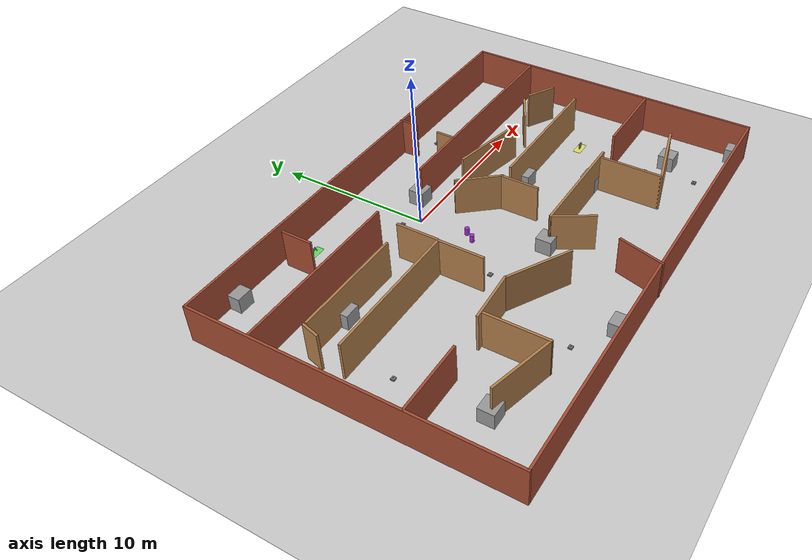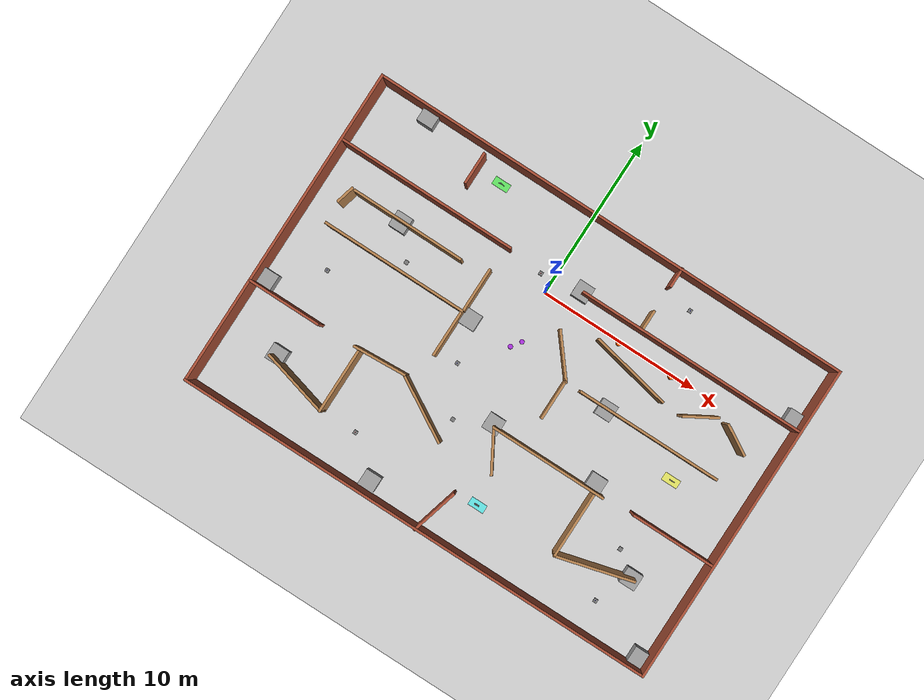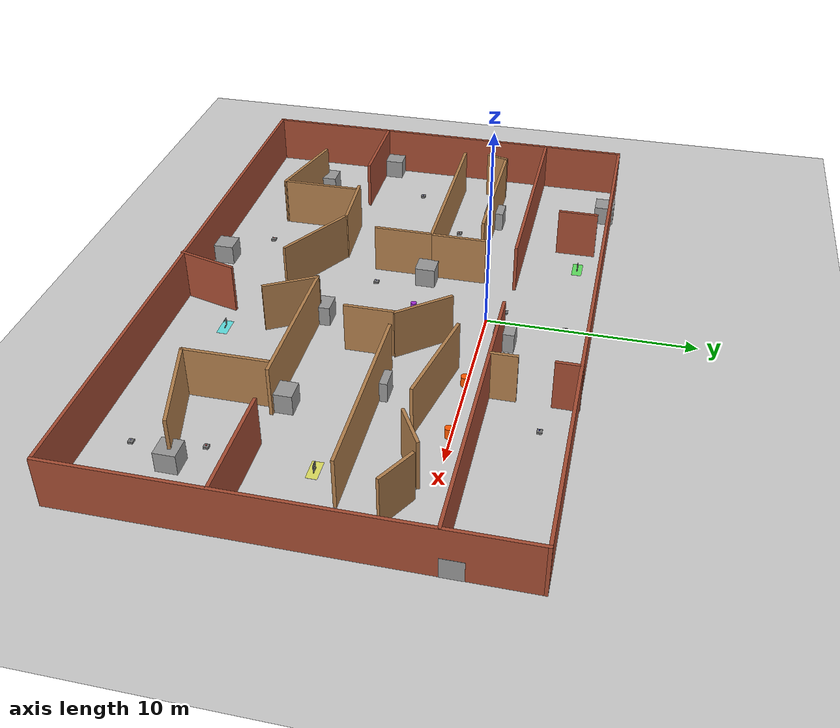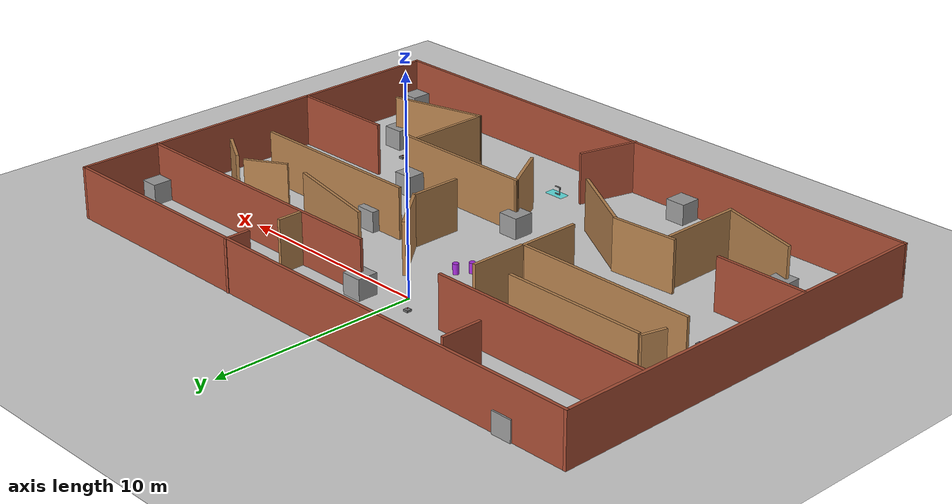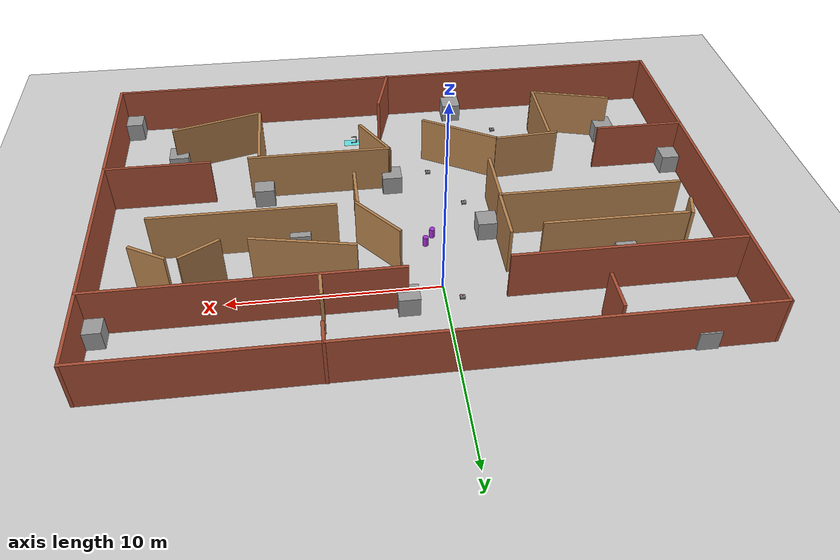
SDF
<sdf version="1.7">
 <world name="my_world">
  <model name="ground_plane">
   <static>1</static>
   <link name="link">
    <collision name="collision">
     <geometry><plane><normal>0 0 1</normal><size>100 100</size></plane></geometry>
     <surface>
      <contact><collide_bitmask>65535</collide_bitmask></contact>
      <friction><ode><mu>100</mu><mu2>50</mu2></ode></friction>
     </surface>
    </collision>
    <visual name="visual">
     <cast_shadows>0</cast_shadows>
     <geometry><plane><normal>0 0 1</normal><size>100 100</size></plane></geometry>
     <material>
      <script><uri>file://media/materials/scripts/gazebo.material</uri><name>Gazebo/Grey</name></script>
     </material>
    </visual>
   </link>
  </model>
  <light name="sun" type="directional">
   <pose>0 0 10 0 -0 0</pose>
   <diffuse>1.0 0.97 0.90 1</diffuse>
   <specular>0.35 0.35 0.35 1</specular>
   <attenuation>
    <range>1000</range>
    <constant>0.9</constant>
    <linear>0.01</linear>
    <quadratic>0.001</quadratic>
   </attenuation>
   <direction>-0.5 0.1 -0.9</direction>
   <spot><inner_angle>0</inner_angle><outer_angle>0</outer_angle><falloff>0</falloff></spot>
  </light>
  <model name="officeroom">
   <pose>0.9981 -4.92976 0 0 -0 0</pose>
   <link name="Wall_10">
    <collision name="Wall_10_Collision">
     <geometry><box><size>20 0.15 2.5</size></box></geometry>
     <pose>0 0 1.25 0 -0 0</pose>
    </collision>
    <visual name="Wall_10_Visual">
     <pose>0 0 1.25 0 -0 0</pose>
     <geometry><box><size>20 0.15 2.5</size></box></geometry>
     <material>
      <script><uri>file://media/materials/scripts/gazebo.material</uri><name>Gazebo/Bricks</name></script>
      <ambient>1 1 1 1</ambient>
     </material>
     <meta><layer>0</layer></meta>
    </visual>
    <pose>14.925 0.014919 0 0 -0 -1.57081</pose>
   </link>
   <link name="Wall_107">
    <collision name="Wall_107_Collision">
     <geometry><box><size>3.27854 0.15 2.5</size></box></geometry>
     <pose>0 0 1.25 0 -0 0</pose>
    </collision>
    <visual name="Wall_107_Visual">
     <pose>0 0 1.25 0 -0 0</pose>
     <geometry><box><size>3.27854 0.15 2.5</size></box></geometry>
     <material>
      <script><uri>file://media/materials/scripts/gazebo.material</uri><name>Gazebo/Wood</name></script>
      <ambient>1 1 1 1</ambient>
     </material>
     <meta><layer>0</layer></meta>
    </visual>
    <pose>-6.58027 -3.242 0 0 -0 -3.08207</pose>
   </link>
   <link name="Wall_109">
    <collision name="Wall_109_Collision">
     <geometry><box><size>4.5 0.15 2.5</size></box></geometry>
     <pose>0 0 1.25 0 -0 0</pose>
    </collision>
    <visual name="Wall_109_Visual">
     <pose>0 0 1.25 0 -0 0</pose>
     <geometry><box><size>4.5 0.15 2.5</size></box></geometry>
     <material>
      <script><uri>file://media/materials/scripts/gazebo.material</uri><name>Gazebo/Bricks</name></script>
      <ambient>1 1 1 1</ambient>
     </material>
     <meta><layer>0</layer></meta>
    </visual>
    <pose>-12.6881 -3.41033 0 0 -0 0</pose>
   </link>
   <link name="Wall_113">
    <collision name="Wall_113_Collision">
     <geometry><box><size>7.25 0.15 2.5</size></box></geometry>
     <pose>0 0 1.25 0 -0 0</pose>
    </collision>
    <visual name="Wall_113_Visual">
     <pose>0 0 1.25 0 -0 0</pose>
     <geometry><box><size>7.25 0.15 2.5</size></box></geometry>
     <material>
      <script><uri>file://media/materials/scripts/gazebo.material</uri><name>Gazebo/Wood</name></script>
      <ambient>1 1 1 1</ambient>
     </material>
     <meta><layer>0</layer></meta>
    </visual>
    <pose>4.22386 -2.91887 0 0 -0 0</pose>
   </link>
   <link name="Wall_115">
    <collision name="Wall_115_Collision">
     <geometry><box><size>5.25 0.15 2.5</size></box></geometry>
     <pose>0 0 1.25 0 -0 0</pose>
    </collision>
    <visual name="Wall_115_Visual">
     <pose>0 0 1.25 0 -0 0</pose>
     <geometry><box><size>5.25 0.15 2.5</size></box></geometry>
     <material>
      <script><uri>file://media/materials/scripts/gazebo.material</uri><name>Gazebo/Bricks</name></script>
      <ambient>1 1 1 1</ambient>
     </material>
     <meta><layer>0</layer></meta>
    </visual>
    <pose>12.3137 -2.7793 0 0 -0 3.14159</pose>
   </link>
   <link name="Wall_118">
    <collision name="Wall_118_Collision">
     <geometry><box><size>2.5 0.15 2.5</size></box></geometry>
     <pose>0 0 1.25 0 -0 0</pose>
    </collision>
    <visual name="Wall_118_Visual">
     <pose>0 0 1.25 0 -0 0</pose>
     <geometry><box><size>2.5 0.15 2.5</size></box></geometry>
     <material>
      <script><uri>file://media/materials/scripts/gazebo.material</uri><name>Gazebo/Wood</name></script>
      <ambient>1 1 1 1</ambient>
     </material>
     <meta><layer>0</layer></meta>
    </visual>
    <pose>2.60295 0.147134 0 0 -0 -1.5708</pose>
   </link>
   <link name="Wall_12">
    <collision name="Wall_12_Collision">
     <geometry><box><size>30 0.15 2.5</size></box></geometry>
     <pose>0 0 1.25 0 -0 0</pose>
    </collision>
    <visual name="Wall_12_Visual">
     <pose>0 0 1.25 0 -0 0</pose>
     <geometry><box><size>30 0.15 2.5</size></box></geometry>
     <material>
      <script><uri>file://media/materials/scripts/gazebo.material</uri><name>Gazebo/Bricks</name></script>
      <ambient>1 1 1 1</ambient>
     </material>
     <meta><layer>0</layer></meta>
    </visual>
    <pose>-0.000162 -9.90993 0 0 -0 3.14159</pose>
   </link>
   <link name="Wall_120">
    <collision name="Wall_120_Collision">
     <geometry><box><size>2.75 0.15 2.5</size></box></geometry>
     <pose>0 0 1.25 0 -0 0</pose>
    </collision>
    <visual name="Wall_120_Visual">
     <pose>0 0 1.25 0 -0 0</pose>
     <geometry><box><size>2.75 0.15 2.5</size></box></geometry>
     <material>
      <script><uri>file://media/materials/scripts/gazebo.material</uri><name>Gazebo/Wood</name></script>
      <ambient>1 1 1 1</ambient>
     </material>
     <meta><layer>0</layer></meta>
    </visual>
    <pose>1.32386 -4.0447 0 0 -0 -1.0472</pose>
   </link>
   <link name="Wall_125">
    <collision name="Wall_125_Collision">
     <geometry><box><size>4 0.15 2.5</size></box></geometry>
     <pose>0 0 1.25 0 -0 0</pose>
    </collision>
    <visual name="Wall_125_Visual">
     <pose>0 0 1.25 0 -0 0</pose>
     <geometry><box><size>4 0.15 2.5</size></box></geometry>
     <material>
      <script><uri>file://media/materials/scripts/gazebo.material</uri><name>Gazebo/Wood</name></script>
      <ambient>1 1 1 1</ambient>
     </material>
     <meta><layer>0</layer></meta>
    </visual>
    <pose>-7.82101 -5.406 0 0 -0 -1.5708</pose>
   </link>
   <link name="Wall_127">
    <collision name="Wall_127_Collision">
     <geometry><box><size>4 0.15 2.5</size></box></geometry>
     <pose>0 0 1.25 0 -0 0</pose>
    </collision>
    <visual name="Wall_127_Visual">
     <pose>0 0 1.25 0 -0 0</pose>
     <geometry><box><size>4 0.15 2.5</size></box></geometry>
     <material>
      <script><uri>file://media/materials/scripts/gazebo.material</uri><name>Gazebo/Wood</name></script>
      <ambient>1 1 1 1</ambient>
     </material>
     <meta><layer>0</layer></meta>
    </visual>
    <pose>7.28181 -5.01384 0 0 -0 -1.5708</pose>
   </link>
   <link name="Wall_129">
    <collision name="Wall_129_Collision">
     <geometry><box><size>4.25 0.15 2.5</size></box></geometry>
     <pose>0 0 1.25 0 -0 0</pose>
    </collision>
    <visual name="Wall_129_Visual">
     <pose>0 0 1.25 0 -0 0</pose>
     <geometry><box><size>4.25 0.15 2.5</size></box></geometry>
     <material>
      <script><uri>file://media/materials/scripts/gazebo.material</uri><name>Gazebo/Wood</name></script>
      <ambient>1 1 1 1</ambient>
     </material>
     <meta><layer>0</layer></meta>
    </visual>
    <pose>-9.80116 -6.80042 0 0 -0 2.87979</pose>
   </link>
   <link name="Wall_132">
    <collision name="Wall_132_Collision">
     <geometry><box><size>4.75 0.15 2.5</size></box></geometry>
     <pose>0 0 1.25 0 -0 0</pose>
    </collision>
    <visual name="Wall_132_Visual">
     <pose>0 0 1.25 0 -0 0</pose>
     <geometry><box><size>4.75 0.15 2.5</size></box></geometry>
     <material>
      <script><uri>file://media/materials/scripts/gazebo.material</uri><name>Gazebo/Wood</name></script>
      <ambient>1 1 1 1</ambient>
     </material>
     <meta><layer>0</layer></meta>
    </visual>
    <pose>9.51735 -6.40461 0 0 -0 0.261799</pose>
   </link>
   <link name="Wall_134">
    <collision name="Wall_134_Collision">
     <geometry><box><size>3 0.15 2.5</size></box></geometry>
     <pose>0 0 1.25 0 -0 0</pose>
    </collision>
    <visual name="Wall_134_Visual">
     <pose>0 0 1.25 0 -0 0</pose>
     <geometry><box><size>3 0.15 2.5</size></box></geometry>
     <material>
      <script><uri>file://media/materials/scripts/gazebo.material</uri><name>Gazebo/Bricks</name></script>
      <ambient>1 1 1 1</ambient>
     </material>
     <meta><layer>0</layer></meta>
    </visual>
    <pose>0.445972 -8.57754 0 0 -0 1.309</pose>
   </link>
   <link name="Wall_15">
    <collision name="Wall_15_Collision">
     <geometry><box><size>20 0.15 2.5</size></box></geometry>
     <pose>0 0 1.25 0 -0 0</pose>
    </collision>
    <visual name="Wall_15_Visual">
     <pose>0 0 1.25 0 -0 0</pose>
     <geometry><box><size>20 0.15 2.5</size></box></geometry>
     <material>
      <script><uri>file://media/materials/scripts/gazebo.material</uri><name>Gazebo/Bricks</name></script>
      <ambient>1 1 1 1</ambient>
     </material>
     <meta><layer>0</layer></meta>
    </visual>
    <pose>-14.9252 0.015073 0 0 -0 1.5708</pose>
   </link>
   <link name="Wall_2">
    <collision name="Wall_2_Collision">
     <geometry><box><size>30 0.15 2.5</size></box></geometry>
     <pose>0 0 1.25 0 -0 0</pose>
    </collision>
    <visual name="Wall_2_Visual">
     <pose>0 0 1.25 0 -0 0</pose>
     <geometry><box><size>30 0.15 2.5</size></box></geometry>
     <material>
      <script><uri>file://media/materials/scripts/gazebo.material</uri><name>Gazebo/Bricks</name></script>
      <ambient>1 1 1 1</ambient>
     </material>
     <meta><layer>0</layer></meta>
    </visual>
    <pose>0.000163 9.93976 0 0 -0 0</pose>
   </link>
   <link name="Wall_29">
    <collision name="Wall_29_Collision">
     <geometry><box><size>1.25 0.15 2.5</size></box></geometry>
     <pose>0 0 1.25 0 -0 0</pose>
    </collision>
    <visual name="Wall_29_Visual">
     <pose>0 0 1.25 0 -0 0</pose>
     <geometry><box><size>1.25 0.15 2.5</size></box></geometry>
     <material>
      <script><uri>file://media/materials/scripts/gazebo.material</uri><name>Gazebo/Bricks</name></script>
      <ambient>1 1 1 1</ambient>
     </material>
     <meta><layer>0</layer></meta>
    </visual>
    <pose>4.61028 9.42084 0 0 -0 -1.5708</pose>
   </link>
   <link name="Wall_31">
    <collision name="Wall_31_Collision">
     <geometry><box><size>1.25 0.15 2.5</size></box></geometry>
     <pose>0 0 1.25 0 -0 0</pose>
    </collision>
    <visual name="Wall_31_Visual">
     <pose>0 0 1.25 0 -0 0</pose>
     <geometry><box><size>1.25 0.15 2.5</size></box></geometry>
     <material>
      <script><uri>file://media/materials/scripts/gazebo.material</uri><name>Gazebo/Wood</name></script>
      <ambient>1 1 1 1</ambient>
     </material>
     <meta><layer>0</layer></meta>
    </visual>
    <pose>4.59016 6.61881 0 0 -0 1.5708</pose>
   </link>
   <link name="Wall_34">
    <collision name="Wall_34_Collision">
     <geometry><box><size>2 0.15 2.5</size></box></geometry>
     <pose>0 0 1.25 0 -0 0</pose>
    </collision>
    <visual name="Wall_34_Visual">
     <pose>0 0 1.25 0 -0 0</pose>
     <geometry><box><size>2 0.15 2.5</size></box></geometry>
     <material>
      <script><uri>file://media/materials/scripts/gazebo.material</uri><name>Gazebo/Bricks</name></script>
      <ambient>1 1 1 1</ambient>
     </material>
     <meta><layer>0</layer></meta>
    </visual>
    <pose>-7.92097 8.43964 0 0 -0 -1.5708</pose>
   </link>
   <link name="Wall_38">
    <collision name="Wall_38_Collision">
     <geometry><box><size>11 0.15 2.5</size></box></geometry>
     <pose>0 0 1.25 0 -0 0</pose>
    </collision>
    <visual name="Wall_38_Visual">
     <pose>0 0 1.25 0 -0 0</pose>
     <geometry><box><size>11 0.15 2.5</size></box></geometry>
     <material>
      <script><uri>file://media/materials/scripts/gazebo.material</uri><name>Gazebo/Bricks</name></script>
      <ambient>1 1 1 1</ambient>
     </material>
     <meta><layer>0</layer></meta>
    </visual>
    <pose>-9.35541 5.8262 0 0 -0 0</pose>
   </link>
   <link name="Wall_40">
    <collision name="Wall_40_Collision">
     <geometry><box><size>14.25 0.15 2.5</size></box></geometry>
     <pose>0 0 1.25 0 -0 0</pose>
    </collision>
    <visual name="Wall_40_Visual">
     <pose>0 0 1.25 0 -0 0</pose>
     <geometry><box><size>14.25 0.15 2.5</size></box></geometry>
     <material>
      <script><uri>file://media/materials/scripts/gazebo.material</uri><name>Gazebo/Bricks</name></script>
      <ambient>1 1 1 1</ambient>
     </material>
     <meta><layer>0</layer></meta>
    </visual>
    <pose>7.83962 5.98375 0 0 -0 3.14159</pose>
   </link>
   <link name="Wall_46">
    <collision name="Wall_46_Collision">
     <geometry><box><size>7.0 0.15 2.5</size></box></geometry>
     <pose>0 0 1.25 0 -0 0</pose>
    </collision>
    <visual name="Wall_46_Visual">
     <pose>0 0 1.25 0 -0 0</pose>
     <geometry><box><size>7.0 0.15 2.5</size></box></geometry>
     <material>
      <script><uri>file://media/materials/scripts/gazebo.material</uri><name>Gazebo/Wood</name></script>
      <ambient>1 1 1 1</ambient>
     </material>
     <meta><layer>0</layer></meta>
    </visual>
    <pose>-9.30884 3.8355 0 0 -0 -0.004163</pose>
   </link>
   <link name="Wall_49">
    <collision name="Wall_49_Collision">
     <geometry><box><size>1.17019 0.15 2.5</size></box></geometry>
     <pose>0 0 1.25 0 -0 0</pose>
    </collision>
    <visual name="Wall_49_Visual">
     <pose>0 0 1.25 0 -0 0</pose>
     <geometry><box><size>1.17019 0.15 2.5</size></box></geometry>
     <material>
      <script><uri>file://media/materials/scripts/gazebo.material</uri><name>Gazebo/Wood</name></script>
      <ambient>1 1 1 1</ambient>
     </material>
     <meta><layer>0</layer></meta>
    </visual>
    <pose>-13.076 3.35727 0 0 -0 -1.82702</pose>
   </link>
   <link name="Wall_57">
    <collision name="Wall_57_Collision">
     <geometry><box><size>2.75 0.15 2.5</size></box></geometry>
     <pose>0 0 1.25 0 -0 0</pose>
    </collision>
    <visual name="Wall_57_Visual">
     <pose>0 0 1.25 0 -0 0</pose>
     <geometry><box><size>2.75 0.15 2.5</size></box></geometry>
     <material>
      <script><uri>file://media/materials/scripts/gazebo.material</uri><name>Gazebo/Wood</name></script>
      <ambient>1 1 1 1</ambient>
     </material>
     <meta><layer>0</layer></meta>
    </visual>
    <pose>-4.21161 2.89682 0 0 -0 1.5708</pose>
   </link>
   <link name="Wall_59">
    <collision name="Wall_59_Collision">
     <geometry><box><size>5.0 0.15 2.5</size></box></geometry>
     <pose>0 0 1.25 0 -0 0</pose>
    </collision>
    <visual name="Wall_59_Visual">
     <pose>0 0 1.25 0 -0 0</pose>
     <geometry><box><size>5.0 0.15 2.5</size></box></geometry>
     <material>
      <script><uri>file://media/materials/scripts/gazebo.material</uri><name>Gazebo/Wood</name></script>
      <ambient>1 1 1 1</ambient>
     </material>
     <meta><layer>0</layer></meta>
    </visual>
    <pose>5.28704 3.77735 0 0 -0 -0.202428</pose>
   </link>
   <link name="Wall_60">
    <collision name="Wall_60_Collision">
     <geometry><box><size>2.1 0.15 2.5</size></box></geometry>
     <pose>0 0 1.25 0 -0 0</pose>
    </collision>
    <visual name="Wall_60_Visual">
     <pose>0 0 1.25 0 -0 0</pose>
     <geometry><box><size>2.1 0.15 2.5</size></box></geometry>
     <material>
      <script><uri>file://media/materials/scripts/gazebo.material</uri><name>Gazebo/Wood</name></script>
      <ambient>1 1 1 1</ambient>
     </material>
     <meta><layer>0</layer></meta>
    </visual>
    <pose>9.88652 3.73459 0 0 -0 0.527727</pose>
   </link>
   <link name="Wall_61">
    <collision name="Wall_61_Collision">
     <geometry><box><size>2.0 0.15 2.5</size></box></geometry>
     <pose>0 0 1.25 0 -0 0</pose>
    </collision>
    <visual name="Wall_61_Visual">
     <pose>0 0 1.25 0 -0 0</pose>
     <geometry><box><size>2.0 0.15 2.5</size></box></geometry>
     <material>
      <script><uri>file://media/materials/scripts/gazebo.material</uri><name>Gazebo/Wood</name></script>
      <ambient>1 1 1 1</ambient>
     </material>
     <meta><layer>0</layer></meta>
    </visual>
    <pose>12.2003 3.7238 0 0 -0 -0.523599</pose>
   </link>
   <link name="Wall_66">
    <collision name="Wall_66_Collision">
     <geometry><box><size>3.01901 0.15 2.5</size></box></geometry>
     <pose>0 0 1.25 0 -0 0</pose>
    </collision>
    <visual name="Wall_66_Visual">
     <pose>0 0 1.25 0 -0 0</pose>
     <geometry><box><size>3.01901 0.15 2.5</size></box></geometry>
     <material>
      <script><uri>file://media/materials/scripts/gazebo.material</uri><name>Gazebo/Wood</name></script>
      <ambient>1 1 1 1</ambient>
     </material>
     <meta><layer>0</layer></meta>
    </visual>
    <pose>1.74226 2.43334 0 0 -0 2.25548</pose>
   </link>
   <link name="Wall_68">
    <collision name="Wall_68_Collision">
     <geometry><box><size>9 0.15 2.5</size></box></geometry>
     <pose>0 0 1.25 0 -0 0</pose>
    </collision>
    <visual name="Wall_68_Visual">
     <pose>0 0 1.25 0 -0 0</pose>
     <geometry><box><size>9 0.15 2.5</size></box></geometry>
     <material>
      <script><uri>file://media/materials/scripts/gazebo.material</uri><name>Gazebo/Wood</name></script>
      <ambient>1 1 1 1</ambient>
     </material>
     <meta><layer>0</layer></meta>
    </visual>
    <pose>-8.68528 1.49923 0 0 -0 3.14159</pose>
   </link>
   <link name="Wall_72">
    <collision name="Wall_72_Collision">
     <geometry><box><size>8.9356 0.15 2.5</size></box></geometry>
     <pose>0 0 1.25 0 -0 0</pose>
    </collision>
    <visual name="Wall_72_Visual">
     <pose>0 0 1.25 0 -0 0</pose>
     <geometry><box><size>8.9356 0.15 2.5</size></box></geometry>
     <material>
      <script><uri>file://media/materials/scripts/gazebo.material</uri><name>Gazebo/Wood</name></script>
      <ambient>1 1 1 1</ambient>
     </material>
     <meta><layer>0</layer></meta>
    </visual>
    <pose>8.04226 1.32213 0 0 -0 3.14159</pose>
   </link>
   <link name="Wall_75">
    <collision name="Wall_75_Collision">
     <geometry><box><size>3 0.15 2.5</size></box></geometry>
     <pose>0 0 1.25 0 -0 0</pose>
    </collision>
    <visual name="Wall_75_Visual">
     <pose>0 0 1.25 0 -0 0</pose>
     <geometry><box><size>3 0.15 2.5</size></box></geometry>
     <material>
      <script><uri>file://media/materials/scripts/gazebo.material</uri><name>Gazebo/Wood</name></script>
      <ambient>1 1 1 1</ambient>
     </material>
     <meta><layer>0</layer></meta>
    </visual>
    <pose>-4.26028 0.074229 0 0 -0 -1.5708</pose>
   </link>
   <link name="Wall_81">
    <collision name="Wall_81_Collision">
     <geometry><box><size>4.25 0.15 2.5</size></box></geometry>
     <pose>0 0 1.25 0 -0 0</pose>
    </collision>
    <visual name="Wall_81_Visual">
     <pose>0 0 1.25 0 -0 0</pose>
     <geometry><box><size>4.25 0.15 2.5</size></box></geometry>
     <material>
      <script><uri>file://media/materials/scripts/gazebo.material</uri><name>Gazebo/Wood</name></script>
      <ambient>1 1 1 1</ambient>
     </material>
     <meta><layer>0</layer></meta>
    </visual>
    <pose>-3.1969 -4.22048 0 0 -0 -0.523599</pose>
   </link>
   <static>1</static>
  </model>
  <gravity>0 0 -9.8</gravity>
  <magnetic_field>6e-06 2.3e-05 -4.2e-05</magnetic_field>
  <atmosphere type="adiabatic"/>
  <physics type="ode">
   <max_step_size>0.002</max_step_size>
   <real_time_factor>1</real_time_factor>
   <real_time_update_rate>500</real_time_update_rate>
  </physics>
  <scene>
   <ambient>0.55 0.56 0.58 1</ambient>
   <background>0.72 0.78 0.86 1</background>
   <shadows>0</shadows>
  </scene>
  <audio><device>default</device></audio>
  <spherical_coordinates>
   <surface_model>EARTH_WGS84</surface_model>
   <latitude_deg>0</latitude_deg>
   <longitude_deg>0</longitude_deg>
   <elevation>0</elevation>
   <heading_deg>0</heading_deg>
  </spherical_coordinates>
  <model name="competition_red_pickup_tray">
   <static>true</static>
   <pose>-7.5 -2.8 0.05 0 0 1.5707963268</pose>
   <link name="tray">
    <collision name="collision">
     <geometry><box><size>0.24 0.24 0.10</size></box></geometry>
     <surface><friction><ode><mu>10</mu><mu2>10</mu2></ode></friction></surface>
    </collision>
    <visual name="visual">
     <geometry><box><size>0.24 0.24 0.10</size></box></geometry>
     <material><ambient>0.35 0.35 0.35 1</ambient><diffuse>0.45 0.45 0.45 1</diffuse></material>
    </visual>
   </link>
  </model>
  <model name="competition_red_pickup_tray_2">
   <static>true</static>
   <pose>-0.8 0.8 0.05 0 0 1.5707963268</pose>
   <link name="tray">
    <collision name="collision">
     <geometry><box><size>0.24 0.24 0.10</size></box></geometry>
     <surface><friction><ode><mu>10</mu><mu2>10</mu2></ode></friction></surface>
    </collision>
    <visual name="visual">
     <geometry><box><size>0.24 0.24 0.10</size></box></geometry>
     <material><ambient>0.35 0.35 0.35 1</ambient><diffuse>0.45 0.45 0.45 1</diffuse></material>
    </visual>
   </link>
  </model>
  <model name="competition_red_pickup_tray_3">
   <static>true</static>
   <pose>0.0 3.8 0.05 0 0 1.5707963268</pose>
   <link name="tray">
    <collision name="collision">
     <geometry><box><size>0.24 0.24 0.10</size></box></geometry>
     <surface><friction><ode><mu>10</mu><mu2>10</mu2></ode></friction></surface>
    </collision>
    <visual name="visual">
     <geometry><box><size>0.24 0.24 0.10</size></box></geometry>
     <material><ambient>0.35 0.35 0.35 1</ambient><diffuse>0.45 0.45 0.45 1</diffuse></material>
    </visual>
   </link>
  </model>
  <model name="competition_red_pickup_tray_4">
   <static>true</static>
   <pose>11.4 -9.8 0.05 0 0 1.5707963268</pose>
   <link name="tray">
    <collision name="collision">
     <geometry><box><size>0.24 0.24 0.10</size></box></geometry>
     <surface><friction><ode><mu>10</mu><mu2>10</mu2></ode></friction></surface>
    </collision>
    <visual name="visual">
     <geometry><box><size>0.24 0.24 0.10</size></box></geometry>
     <material><ambient>0.35 0.35 0.35 1</ambient><diffuse>0.45 0.45 0.45 1</diffuse></material>
    </visual>
   </link>
  </model>
  <model name="competition_red_pickup_tray_5">
   <static>true</static>
   <pose>-4.7 -12.4 0.05 0 0 1.5707963268</pose>
   <link name="tray">
    <collision name="collision">
     <geometry><box><size>0.24 0.24 0.10</size></box></geometry>
     <surface><friction><ode><mu>10</mu><mu2>10</mu2></ode></friction></surface>
    </collision>
    <visual name="visual">
     <geometry><box><size>0.24 0.24 0.10</size></box></geometry>
     <material><ambient>0.35 0.35 0.35 1</ambient><diffuse>0.45 0.45 0.45 1</diffuse></material>
    </visual>
   </link>
  </model>
  <model name="competition_blue_pickup_tray">
   <static>true</static>
   <pose>7.4 3.6 0.05 0 0 1.5707963268</pose>
   <link name="tray">
    <collision name="collision">
     <geometry><box><size>0.24 0.24 0.10</size></box></geometry>
     <surface><friction><ode><mu>10</mu><mu2>10</mu2></ode></friction></surface>
    </collision>
    <visual name="visual">
     <geometry><box><size>0.24 0.24 0.10</size></box></geometry>
     <material><ambient>0.35 0.35 0.35 1</ambient><diffuse>0.45 0.45 0.45 1</diffuse></material>
    </visual>
   </link>
  </model>
  <model name="competition_blue_pickup_tray_2">
   <static>true</static>
   <pose>-11.0 -5.6 0.05 0 0 1.5707963268</pose>
   <link name="tray">
    <collision name="collision">
     <geometry><box><size>0.24 0.24 0.10</size></box></geometry>
     <surface><friction><ode><mu>10</mu><mu2>10</mu2></ode></friction></surface>
    </collision>
    <visual name="visual">
     <geometry><box><size>0.24 0.24 0.10</size></box></geometry>
     <material><ambient>0.35 0.35 0.35 1</ambient><diffuse>0.45 0.45 0.45 1</diffuse></material>
    </visual>
   </link>
  </model>
  <model name="competition_blue_pickup_tray_3">
   <static>true</static>
   <pose>-2.0 -6.0 0.05 0 0 1.5707963268</pose>
   <link name="tray">
    <collision name="collision">
     <geometry><box><size>0.24 0.24 0.10</size></box></geometry>
     <surface><friction><ode><mu>10</mu><mu2>10</mu2></ode></friction></surface>
    </collision>
    <visual name="visual">
     <geometry><box><size>0.24 0.24 0.10</size></box></geometry>
     <material><ambient>0.35 0.35 0.35 1</ambient><diffuse>0.45 0.45 0.45 1</diffuse></material>
    </visual>
   </link>
  </model>
  <model name="competition_blue_pickup_tray_4">
   <static>true</static>
   <pose>-0.5 -8.8 0.05 0 0 1.5707963268</pose>
   <link name="tray">
    <collision name="collision">
     <geometry><box><size>0.24 0.24 0.10</size></box></geometry>
     <surface><friction><ode><mu>10</mu><mu2>10</mu2></ode></friction></surface>
    </collision>
    <visual name="visual">
     <geometry><box><size>0.24 0.24 0.10</size></box></geometry>
     <material><ambient>0.35 0.35 0.35 1</ambient><diffuse>0.45 0.45 0.45 1</diffuse></material>
    </visual>
   </link>
  </model>
  <model name="competition_blue_pickup_tray_5">
   <static>true</static>
   <pose>11.8 -13.0 0.05 0 0 1.5707963268</pose>
   <link name="tray">
    <collision name="collision">
     <geometry><box><size>0.24 0.24 0.10</size></box></geometry>
     <surface><friction><ode><mu>10</mu><mu2>10</mu2></ode></friction></surface>
    </collision>
    <visual name="visual">
     <geometry><box><size>0.24 0.24 0.10</size></box></geometry>
     <material><ambient>0.35 0.35 0.35 1</ambient><diffuse>0.45 0.45 0.45 1</diffuse></material>
    </visual>
   </link>
  </model>
  <model name="red_cube_1">
   <pose>-7.5 -2.8 0.13 0 0 0</pose>
   <link name="link">
    <inertial>
     <mass>0.005</mass>
     <inertia>
      <ixx>0.00000075</ixx>
      <ixy>0</ixy>
      <ixz>0</ixz>
      <iyy>0.00000075</iyy>
      <iyz>0</iyz>
      <izz>0.00000075</izz>
     </inertia>
    </inertial>
    <collision name="collision">
     <geometry><box><size>0.03 0.03 0.03</size></box></geometry>
     <surface>
      <contact>
       <ode>
        <soft_cfm>0.001</soft_cfm>
        <soft_erp>0.2</soft_erp>
        <max_vel>0.1</max_vel>
        <min_depth>0.001</min_depth>
       </ode>
      </contact>
      <friction><ode><mu>0.01</mu><mu2>0.01</mu2></ode></friction>
     </surface>
    </collision>
    <visual name="visual">
     <geometry><box><size>0.03 0.03 0.03</size></box></geometry>
     <material><ambient>1 0 0 1</ambient><diffuse>1 0 0 1</diffuse></material>
    </visual>
   </link>
  </model>
  <model name="red_cube_2">
   <pose>-0.8 0.8 0.13 0 0 0</pose>
   <link name="link">
    <inertial>
     <mass>0.005</mass>
     <inertia>
      <ixx>0.00000075</ixx>
      <ixy>0</ixy>
      <ixz>0</ixz>
      <iyy>0.00000075</iyy>
      <iyz>0</iyz>
      <izz>0.00000075</izz>
     </inertia>
    </inertial>
    <collision name="collision">
     <geometry><box><size>0.03 0.03 0.03</size></box></geometry>
     <surface>
      <contact>
       <ode>
        <soft_cfm>0.001</soft_cfm>
        <soft_erp>0.2</soft_erp>
        <max_vel>0.1</max_vel>
        <min_depth>0.001</min_depth>
       </ode>
      </contact>
      <friction><ode><mu>0.01</mu><mu2>0.01</mu2></ode></friction>
     </surface>
    </collision>
    <visual name="visual">
     <geometry><box><size>0.03 0.03 0.03</size></box></geometry>
     <material><ambient>1 0 0 1</ambient><diffuse>1 0 0 1</diffuse></material>
    </visual>
   </link>
  </model>
  <model name="red_cube_3">
   <pose>0.0 3.8 0.13 0 0 0</pose>
   <link name="link">
    <inertial>
     <mass>0.005</mass>
     <inertia>
      <ixx>0.00000075</ixx>
      <ixy>0</ixy>
      <ixz>0</ixz>
      <iyy>0.00000075</iyy>
      <iyz>0</iyz>
      <izz>0.00000075</izz>
     </inertia>
    </inertial>
    <collision name="collision">
     <geometry><box><size>0.03 0.03 0.03</size></box></geometry>
     <surface>
      <contact>
       <ode>
        <soft_cfm>0.001</soft_cfm>
        <soft_erp>0.2</soft_erp>
        <max_vel>0.1</max_vel>
        <min_depth>0.001</min_depth>
       </ode>
      </contact>
      <friction><ode><mu>0.01</mu><mu2>0.01</mu2></ode></friction>
     </surface>
    </collision>
    <visual name="visual">
     <geometry><box><size>0.03 0.03 0.03</size></box></geometry>
     <material><ambient>1 0 0 1</ambient><diffuse>1 0 0 1</diffuse></material>
    </visual>
   </link>
  </model>
  <model name="red_cube_4">
   <pose>11.4 -9.8 0.13 0 0 0</pose>
   <link name="link">
    <inertial>
     <mass>0.005</mass>
     <inertia>
      <ixx>0.00000075</ixx>
      <ixy>0</ixy>
      <ixz>0</ixz>
      <iyy>0.00000075</iyy>
      <iyz>0</iyz>
      <izz>0.00000075</izz>
     </inertia>
    </inertial>
    <collision name="collision">
     <geometry><box><size>0.03 0.03 0.03</size></box></geometry>
     <surface>
      <contact>
       <ode>
        <soft_cfm>0.001</soft_cfm>
        <soft_erp>0.2</soft_erp>
        <max_vel>0.1</max_vel>
        <min_depth>0.001</min_depth>
       </ode>
      </contact>
      <friction><ode><mu>0.01</mu><mu2>0.01</mu2></ode></friction>
     </surface>
    </collision>
    <visual name="visual">
     <geometry><box><size>0.03 0.03 0.03</size></box></geometry>
     <material><ambient>1 0 0 1</ambient><diffuse>1 0 0 1</diffuse></material>
    </visual>
   </link>
  </model>
  <model name="red_cube_5">
   <pose>-4.7 -12.4 0.13 0 0 0</pose>
   <link name="link">
    <inertial>
     <mass>0.005</mass>
     <inertia>
      <ixx>0.00000075</ixx>
      <ixy>0</ixy>
      <ixz>0</ixz>
      <iyy>0.00000075</iyy>
      <iyz>0</iyz>
      <izz>0.00000075</izz>
     </inertia>
    </inertial>
    <collision name="collision">
     <geometry><box><size>0.03 0.03 0.03</size></box></geometry>
     <surface>
      <contact>
       <ode>
        <soft_cfm>0.001</soft_cfm>
        <soft_erp>0.2</soft_erp>
        <max_vel>0.1</max_vel>
        <min_depth>0.001</min_depth>
       </ode>
      </contact>
      <friction><ode><mu>0.01</mu><mu2>0.01</mu2></ode></friction>
     </surface>
    </collision>
    <visual name="visual">
     <geometry><box><size>0.03 0.03 0.03</size></box></geometry>
     <material><ambient>1 0 0 1</ambient><diffuse>1 0 0 1</diffuse></material>
    </visual>
   </link>
  </model>
  <model name="blue_cube_1">
   <pose>7.4 3.6 0.13 0 0 0</pose>
   <link name="link">
    <inertial>
     <mass>0.005</mass>
     <inertia>
      <ixx>0.00000075</ixx>
      <ixy>0</ixy>
      <ixz>0</ixz>
      <iyy>0.00000075</iyy>
      <iyz>0</iyz>
      <izz>0.00000075</izz>
     </inertia>
    </inertial>
    <collision name="collision">
     <geometry><box><size>0.03 0.03 0.03</size></box></geometry>
     <surface>
      <contact>
       <ode>
        <soft_cfm>0.001</soft_cfm>
        <soft_erp>0.2</soft_erp>
        <max_vel>0.1</max_vel>
        <min_depth>0.001</min_depth>
       </ode>
      </contact>
      <friction><ode><mu>0.01</mu><mu2>0.01</mu2></ode></friction>
     </surface>
    </collision>
    <visual name="visual">
     <geometry><box><size>0.03 0.03 0.03</size></box></geometry>
     <material><ambient>0 0 1 1</ambient><diffuse>0 0 1 1</diffuse></material>
    </visual>
   </link>
  </model>
  <model name="blue_cube_2">
   <pose>-11.0 -5.6 0.13 0 0 0</pose>
   <link name="link">
    <inertial>
     <mass>0.005</mass>
     <inertia>
      <ixx>0.00000075</ixx>
      <ixy>0</ixy>
      <ixz>0</ixz>
      <iyy>0.00000075</iyy>
      <iyz>0</iyz>
      <izz>0.00000075</izz>
     </inertia>
    </inertial>
    <collision name="collision">
     <geometry><box><size>0.03 0.03 0.03</size></box></geometry>
     <surface>
      <contact>
       <ode>
        <soft_cfm>0.001</soft_cfm>
        <soft_erp>0.2</soft_erp>
        <max_vel>0.1</max_vel>
        <min_depth>0.001</min_depth>
       </ode>
      </contact>
      <friction><ode><mu>0.01</mu><mu2>0.01</mu2></ode></friction>
     </surface>
    </collision>
    <visual name="visual">
     <geometry><box><size>0.03 0.03 0.03</size></box></geometry>
     <material><ambient>0 0 1 1</ambient><diffuse>0 0 1 1</diffuse></material>
    </visual>
   </link>
  </model>
  <model name="blue_cube_3">
   <pose>-2.0 -6.0 0.13 0 0 0</pose>
   <link name="link">
    <inertial>
     <mass>0.005</mass>
     <inertia>
      <ixx>0.00000075</ixx>
      <ixy>0</ixy>
      <ixz>0</ixz>
      <iyy>0.00000075</iyy>
      <iyz>0</iyz>
      <izz>0.00000075</izz>
     </inertia>
    </inertial>
    <collision name="collision">
     <geometry><box><size>0.03 0.03 0.03</size></box></geometry>
     <surface>
      <contact>
       <ode>
        <soft_cfm>0.001</soft_cfm>
        <soft_erp>0.2</soft_erp>
        <max_vel>0.1</max_vel>
        <min_depth>0.001</min_depth>
       </ode>
      </contact>
      <friction><ode><mu>0.01</mu><mu2>0.01</mu2></ode></friction>
     </surface>
    </collision>
    <visual name="visual">
     <geometry><box><size>0.03 0.03 0.03</size></box></geometry>
     <material><ambient>0 0 1 1</ambient><diffuse>0 0 1 1</diffuse></material>
    </visual>
   </link>
  </model>
  <model name="blue_cube_4">
   <pose>-0.5 -8.8 0.13 0 0 0</pose>
   <link name="link">
    <inertial>
     <mass>0.005</mass>
     <inertia>
      <ixx>0.00000075</ixx>
      <ixy>0</ixy>
      <ixz>0</ixz>
      <iyy>0.00000075</iyy>
      <iyz>0</iyz>
      <izz>0.00000075</izz>
     </inertia>
    </inertial>
    <collision name="collision">
     <geometry><box><size>0.03 0.03 0.03</size></box></geometry>
     <surface>
      <contact>
       <ode>
        <soft_cfm>0.001</soft_cfm>
        <soft_erp>0.2</soft_erp>
        <max_vel>0.1</max_vel>
        <min_depth>0.001</min_depth>
       </ode>
      </contact>
      <friction><ode><mu>0.01</mu><mu2>0.01</mu2></ode></friction>
     </surface>
    </collision>
    <visual name="visual">
     <geometry><box><size>0.03 0.03 0.03</size></box></geometry>
     <material><ambient>0 0 1 1</ambient><diffuse>0 0 1 1</diffuse></material>
    </visual>
   </link>
  </model>
  <model name="blue_cube_5">
   <pose>11.8 -13.0 0.13 0 0 0</pose>
   <link name="link">
    <inertial>
     <mass>0.005</mass>
     <inertia>
      <ixx>0.00000075</ixx>
      <ixy>0</ixy>
      <ixz>0</ixz>
      <iyy>0.00000075</iyy>
      <iyz>0</iyz>
      <izz>0.00000075</izz>
     </inertia>
    </inertial>
    <collision name="collision">
     <geometry><box><size>0.03 0.03 0.03</size></box></geometry>
     <surface>
      <contact>
       <ode>
        <soft_cfm>0.001</soft_cfm>
        <soft_erp>0.2</soft_erp>
        <max_vel>0.1</max_vel>
        <min_depth>0.001</min_depth>
       </ode>
      </contact>
      <friction><ode><mu>0.01</mu><mu2>0.01</mu2></ode></friction>
     </surface>
    </collision>
    <visual name="visual">
     <geometry><box><size>0.03 0.03 0.03</size></box></geometry>
     <material><ambient>0 0 1 1</ambient><diffuse>0 0 1 1</diffuse></material>
    </visual>
   </link>
  </model>
  <model name="zone_a">
   <static>1</static>
   <pose>-5.4 3.8 0.01 0 0 0</pose>
   <link name="base">
    <visual name="visual">
     <geometry><box><size>1 0.5 0.02</size></box></geometry>
     <material><ambient>0 1 0 0.5</ambient><diffuse>0 1 0 0.5</diffuse></material>
    </visual>
   </link>
   <link name="letter_A_1">
    <pose>-0.1 0 0.22 0 0.4 0</pose>
    <visual name="v">
     <geometry><box><size>0.04 0.04 0.4</size></box></geometry>
     <material><ambient>0 0 0 1</ambient><diffuse>0 0 0 1</diffuse></material>
    </visual>
   </link>
   <link name="letter_A_2">
    <pose>0.1 0 0.22 0 -0.4 0</pose>
    <visual name="v">
     <geometry><box><size>0.04 0.04 0.4</size></box></geometry>
     <material><ambient>0 0 0 1</ambient><diffuse>0 0 0 1</diffuse></material>
    </visual>
   </link>
   <link name="letter_A_3">
    <pose>0 0 0.25 0 -0 0</pose>
    <visual name="v">
     <geometry><box><size>0.15 0.04 0.04</size></box></geometry>
     <material><ambient>0 0 0 1</ambient><diffuse>0 0 0 1</diffuse></material>
    </visual>
   </link>
  </model>
  <model name="zone_b">
   <static>1</static>
   <pose>11.7 -5.0 0.01 0 0 0</pose>
   <link name="base">
    <visual name="visual">
     <geometry><box><size>1 0.5 0.02</size></box></geometry>
     <material><ambient>1 1 0 0.5</ambient><diffuse>1 1 0 0.5</diffuse></material>
    </visual>
   </link>
   <link name="letter_B_vertical_stroke">
    <pose>-0.1 0 0.2 0 -0 0</pose>
    <visual name="v">
     <geometry><box><size>0.04 0.04 0.4</size></box></geometry>
     <material><ambient>0 0 0 1</ambient><diffuse>0 0 0 1</diffuse></material>
    </visual>
   </link>
   <link name="letter_B_top_horizontal">
    <pose>0.05 0 0.38 0 -0 0</pose>
    <visual name="v">
     <geometry><box><size>0.25 0.04 0.04</size></box></geometry>
     <material><ambient>0 0 0 1</ambient><diffuse>0 0 0 1</diffuse></material>
    </visual>
   </link>
   <link name="letter_B_middle_horizontal">
    <pose>0.05 0 0.2 0 -0 0</pose>
    <visual name="v">
     <geometry><box><size>0.25 0.04 0.04</size></box></geometry>
     <material><ambient>0 0 0 1</ambient><diffuse>0 0 0 1</diffuse></material>
    </visual>
   </link>
   <link name="letter_B_bottom_horizontal">
    <pose>0.05 0 0.02 0 -0 0</pose>
    <visual name="v">
     <geometry><box><size>0.25 0.04 0.04</size></box></geometry>
     <material><ambient>0 0 0 1</ambient><diffuse>0 0 0 1</diffuse></material>
    </visual>
   </link>
   <link name="letter_B_top_vertical_stroke">
    <pose>0.15 0 0.29 0 -0 0</pose>
    <visual name="v">
     <geometry><box><size>0.04 0.04 0.2</size></box></geometry>
     <material><ambient>0 0 0 1</ambient><diffuse>0 0 0 1</diffuse></material>
    </visual>
   </link>
   <link name="letter_B_bottom_vertical_stroke">
    <pose>0.15 0 0.11 0 -0 0</pose>
    <visual name="v">
     <geometry><box><size>0.04 0.04 0.2</size></box></geometry>
     <material><ambient>0 0 0 1</ambient><diffuse>0 0 0 1</diffuse></material>
    </visual>
   </link>
  </model>
  <model name="zone_c">
   <static>1</static>
   <pose>3.3 -12.1 0.01 0 0 0</pose>
   <link name="base">
    <visual name="visual">
     <geometry><box><size>1 0.5 0.02</size></box></geometry>
     <material><ambient>0 1 1 0.5</ambient><diffuse>0 1 1 0.5</diffuse></material>
    </visual>
   </link>
   <link name="letter_C_1">
    <pose>-0.05 0 0.38 0 -0 0</pose>
    <visual name="v">
     <geometry><box><size>0.3 0.04 0.04</size></box></geometry>
     <material><ambient>0 0 0 1</ambient><diffuse>0 0 0 1</diffuse></material>
    </visual>
   </link>
   <link name="letter_C_2">
    <pose>-0.05 0 0.02 0 -0 0</pose>
    <visual name="v">
     <geometry><box><size>0.3 0.04 0.04</size></box></geometry>
     <material><ambient>0 0 0 1</ambient><diffuse>0 0 0 1</diffuse></material>
    </visual>
   </link>
   <link name="letter_C_3">
    <pose>-0.18 0 0.2 0 -0 0</pose>
    <visual name="v">
     <geometry><box><size>0.04 0.04 0.4</size></box></geometry>
     <material><ambient>0 0 0 1</ambient><diffuse>0 0 0 1</diffuse></material>
    </visual>
   </link>
  </model>
  <plugin name="gazebo_link_attacher" filename="libgazebo_link_attacher.so"/>
  <model name="Untitled">
   <link name="link_0">
    <inertial>
     <mass>1</mass>
     <inertia>
      <ixx>0.166667</ixx>
      <ixy>0</ixy>
      <ixz>0</ixz>
      <iyy>0.166667</iyy>
      <iyz>0</iyz>
      <izz>0.166667</izz>
     </inertia>
    </inertial>
    <pose>-11.7361 10.376 0 0 -0 0</pose>
    <visual name="visual">
     <geometry><box><size>1 1 1</size></box></geometry>
     <material>
      <lighting>1</lighting>
      <script><uri>file://media/materials/scripts/gazebo.material</uri><name>Gazebo/Grey</name></script>
      <shader type="pixel"/>
     </material>
    </visual>
    <collision name="collision">
     <geometry><box><size>1 1 1</size></box></geometry>
     <surface>
      <friction>
       <ode><mu>1</mu><mu2>1</mu2><fdir1>0 0 0</fdir1><slip1>0</slip1><slip2>0</slip2></ode>
       <torsional>
        <coefficient>1</coefficient>
        <patch_radius>0</patch_radius>
        <surface_radius>0</surface_radius>
        <use_patch_radius>1</use_patch_radius>
        <ode><slip>0</slip></ode>
       </torsional>
      </friction>
      <bounce><restitution_coefficient>0</restitution_coefficient><threshold>1e+06</threshold></bounce>
      <contact>
       <collide_without_contact>0</collide_without_contact>
       <collide_without_contact_bitmask>1</collide_without_contact_bitmask>
       <collide_bitmask>1</collide_bitmask>
       <ode>
        <soft_cfm>0</soft_cfm>
        <soft_erp>0.2</soft_erp>
        <kp>1e+13</kp>
        <kd>1</kd>
        <max_vel>0.01</max_vel>
        <min_depth>0</min_depth>
       </ode>
       <bullet>
        <split_impulse>1</split_impulse>
        <split_impulse_penetration_threshold>-0.01</split_impulse_penetration_threshold>
        <soft_cfm>0</soft_cfm>
        <soft_erp>0.2</soft_erp>
        <kp>1e+13</kp>
        <kd>1</kd>
       </bullet>
      </contact>
     </surface>
    </collision>
   </link>
   <link name="link_1">
    <inertial>
     <mass>1</mass>
     <inertia>
      <ixx>0.166667</ixx>
      <ixy>0</ixy>
      <ixz>0</ixz>
      <iyy>0.166667</iyy>
      <iyz>0</iyz>
      <izz>0.166667</izz>
     </inertia>
    </inertial>
    <pose>-9.86873 4.59948 0 0 -0 0</pose>
    <visual name="visual">
     <geometry><box><size>1 1 1</size></box></geometry>
     <material>
      <lighting>1</lighting>
      <script><uri>file://media/materials/scripts/gazebo.material</uri><name>Gazebo/Grey</name></script>
      <shader type="pixel"/>
     </material>
    </visual>
    <collision name="collision">
     <geometry><box><size>1 1 1</size></box></geometry>
     <surface>
      <friction>
       <ode><mu>1</mu><mu2>1</mu2><fdir1>0 0 0</fdir1><slip1>0</slip1><slip2>0</slip2></ode>
       <torsional>
        <coefficient>1</coefficient>
        <patch_radius>0</patch_radius>
        <surface_radius>0</surface_radius>
        <use_patch_radius>1</use_patch_radius>
        <ode><slip>0</slip></ode>
       </torsional>
      </friction>
      <bounce><restitution_coefficient>0</restitution_coefficient><threshold>1e+06</threshold></bounce>
      <contact>
       <collide_without_contact>0</collide_without_contact>
       <collide_without_contact_bitmask>1</collide_without_contact_bitmask>
       <collide_bitmask>1</collide_bitmask>
       <ode>
        <soft_cfm>0</soft_cfm>
        <soft_erp>0.2</soft_erp>
        <kp>1e+13</kp>
        <kd>1</kd>
        <max_vel>0.01</max_vel>
        <min_depth>0</min_depth>
       </ode>
       <bullet>
        <split_impulse>1</split_impulse>
        <split_impulse_penetration_threshold>-0.01</split_impulse_penetration_threshold>
        <soft_cfm>0</soft_cfm>
        <soft_erp>0.2</soft_erp>
        <kp>1e+13</kp>
        <kd>1</kd>
       </bullet>
      </contact>
     </surface>
    </collision>
   </link>
   <link name="link_10">
    <inertial>
     <mass>1</mass>
     <inertia>
      <ixx>0.166667</ixx>
      <ixy>0</ixy>
      <ixz>0</ixz>
      <iyy>0.166667</iyy>
      <iyz>0</iyz>
      <izz>0.166667</izz>
     </inertia>
    </inertial>
    <pose>11.7248 -5.10078 0 0 -0 0</pose>
    <visual name="visual">
     <geometry><box><size>1 1 1</size></box></geometry>
     <material>
      <lighting>1</lighting>
      <script><uri>file://media/materials/scripts/gazebo.material</uri><name>Gazebo/Grey</name></script>
      <shader type="pixel"/>
     </material>
    </visual>
    <collision name="collision">
     <geometry><box><size>1 1 1</size></box></geometry>
     <surface>
      <friction>
       <ode><mu>1</mu><mu2>1</mu2><fdir1>0 0 0</fdir1><slip1>0</slip1><slip2>0</slip2></ode>
       <torsional>
        <coefficient>1</coefficient>
        <patch_radius>0</patch_radius>
        <surface_radius>0</surface_radius>
        <use_patch_radius>1</use_patch_radius>
        <ode><slip>0</slip></ode>
       </torsional>
      </friction>
      <bounce><restitution_coefficient>0</restitution_coefficient><threshold>1e+06</threshold></bounce>
      <contact>
       <collide_without_contact>0</collide_without_contact>
       <collide_without_contact_bitmask>1</collide_without_contact_bitmask>
       <collide_bitmask>1</collide_bitmask>
       <ode>
        <soft_cfm>0</soft_cfm>
        <soft_erp>0.2</soft_erp>
        <kp>1e+13</kp>
        <kd>1</kd>
        <max_vel>0.01</max_vel>
        <min_depth>0</min_depth>
       </ode>
       <bullet>
        <split_impulse>1</split_impulse>
        <split_impulse_penetration_threshold>-0.01</split_impulse_penetration_threshold>
        <soft_cfm>0</soft_cfm>
        <soft_erp>0.2</soft_erp>
        <kp>1e+13</kp>
        <kd>1</kd>
       </bullet>
      </contact>
     </surface>
    </collision>
   </link>
   <link name="link_11">
    <inertial>
     <mass>1</mass>
     <inertia>
      <ixx>0.166667</ixx>
      <ixy>0</ixy>
      <ixz>0</ixz>
      <iyy>0.166667</iyy>
      <iyz>0</iyz>
      <izz>0.166667</izz>
     </inertia>
    </inertial>
    <pose>-3.47257 -8.45059 0 0 -0 0</pose>
    <visual name="visual">
     <geometry><box><size>1 1 1</size></box></geometry>
     <material>
      <lighting>1</lighting>
      <script><uri>file://media/materials/scripts/gazebo.material</uri><name>Gazebo/Grey</name></script>
      <shader type="pixel"/>
     </material>
    </visual>
    <collision name="collision">
     <geometry><box><size>1 1 1</size></box></geometry>
     <surface>
      <friction>
       <ode><mu>1</mu><mu2>1</mu2><fdir1>0 0 0</fdir1><slip1>0</slip1><slip2>0</slip2></ode>
       <torsional>
        <coefficient>1</coefficient>
        <patch_radius>0</patch_radius>
        <surface_radius>0</surface_radius>
        <use_patch_radius>1</use_patch_radius>
        <ode><slip>0</slip></ode>
       </torsional>
      </friction>
      <bounce><restitution_coefficient>0</restitution_coefficient><threshold>1e+06</threshold></bounce>
      <contact>
       <collide_without_contact>0</collide_without_contact>
       <collide_without_contact_bitmask>1</collide_without_contact_bitmask>
       <collide_bitmask>1</collide_bitmask>
       <ode>
        <soft_cfm>0</soft_cfm>
        <soft_erp>0.2</soft_erp>
        <kp>1e+13</kp>
        <kd>1</kd>
        <max_vel>0.01</max_vel>
        <min_depth>0</min_depth>
       </ode>
       <bullet>
        <split_impulse>1</split_impulse>
        <split_impulse_penetration_threshold>-0.01</split_impulse_penetration_threshold>
        <soft_cfm>0</soft_cfm>
        <soft_erp>0.2</soft_erp>
        <kp>1e+13</kp>
        <kd>1</kd>
       </bullet>
      </contact>
     </surface>
    </collision>
   </link>
   <link name="link_12">
    <inertial>
     <mass>1</mass>
     <inertia>
      <ixx>0.166667</ixx>
      <ixy>0</ixy>
      <ixz>0</ixz>
      <iyy>0.166667</iyy>
      <iyz>0</iyz>
      <izz>0.166667</izz>
     </inertia>
    </inertial>
    <pose>14.5027 -8.59174 0 0 -0 0</pose>
    <visual name="visual">
     <geometry><box><size>1 1 1</size></box></geometry>
     <material>
      <lighting>1</lighting>
      <script><uri>file://media/materials/scripts/gazebo.material</uri><name>Gazebo/Grey</name></script>
      <shader type="pixel"/>
     </material>
    </visual>
    <collision name="collision">
     <geometry><box><size>1 1 1</size></box></geometry>
     <surface>
      <friction>
       <ode><mu>1</mu><mu2>1</mu2><fdir1>0 0 0</fdir1><slip1>0</slip1><slip2>0</slip2></ode>
       <torsional>
        <coefficient>1</coefficient>
        <patch_radius>0</patch_radius>
        <surface_radius>0</surface_radius>
        <use_patch_radius>1</use_patch_radius>
        <ode><slip>0</slip></ode>
       </torsional>
      </friction>
      <bounce><restitution_coefficient>0</restitution_coefficient><threshold>1e+06</threshold></bounce>
      <contact>
       <collide_without_contact>0</collide_without_contact>
       <collide_without_contact_bitmask>1</collide_without_contact_bitmask>
       <collide_bitmask>1</collide_bitmask>
       <ode>
        <soft_cfm>0</soft_cfm>
        <soft_erp>0.2</soft_erp>
        <kp>1e+13</kp>
        <kd>1</kd>
        <max_vel>0.01</max_vel>
        <min_depth>0</min_depth>
       </ode>
       <bullet>
        <split_impulse>1</split_impulse>
        <split_impulse_penetration_threshold>-0.01</split_impulse_penetration_threshold>
        <soft_cfm>0</soft_cfm>
        <soft_erp>0.2</soft_erp>
        <kp>1e+13</kp>
        <kd>1</kd>
       </bullet>
      </contact>
     </surface>
    </collision>
   </link>
   <link name="link_2">
    <inertial>
     <mass>1</mass>
     <inertia>
      <ixx>0.166667</ixx>
      <ixy>0</ixy>
      <ixz>0</ixz>
      <iyy>0.166667</iyy>
      <iyz>0</iyz>
      <izz>0.166667</izz>
     </inertia>
    </inertial>
    <pose>0.764529 6.87658 0 0 -0 0</pose>
    <visual name="visual">
     <geometry><box><size>1 1 1</size></box></geometry>
     <material>
      <lighting>1</lighting>
      <script><uri>file://media/materials/scripts/gazebo.material</uri><name>Gazebo/Grey</name></script>
      <shader type="pixel"/>
     </material>
    </visual>
    <collision name="collision">
     <geometry><box><size>1 1 1</size></box></geometry>
     <surface>
      <friction>
       <ode><mu>1</mu><mu2>1</mu2><fdir1>0 0 0</fdir1><slip1>0</slip1><slip2>0</slip2></ode>
       <torsional>
        <coefficient>1</coefficient>
        <patch_radius>0</patch_radius>
        <surface_radius>0</surface_radius>
        <use_patch_radius>1</use_patch_radius>
        <ode><slip>0</slip></ode>
       </torsional>
      </friction>
      <bounce><restitution_coefficient>0</restitution_coefficient><threshold>1e+06</threshold></bounce>
      <contact>
       <collide_without_contact>0</collide_without_contact>
       <collide_without_contact_bitmask>1</collide_without_contact_bitmask>
       <collide_bitmask>1</collide_bitmask>
       <ode>
        <soft_cfm>0</soft_cfm>
        <soft_erp>0.2</soft_erp>
        <kp>1e+13</kp>
        <kd>1</kd>
        <max_vel>0.01</max_vel>
        <min_depth>0</min_depth>
       </ode>
       <bullet>
        <split_impulse>1</split_impulse>
        <split_impulse_penetration_threshold>-0.01</split_impulse_penetration_threshold>
        <soft_cfm>0</soft_cfm>
        <soft_erp>0.2</soft_erp>
        <kp>1e+13</kp>
        <kd>1</kd>
       </bullet>
      </contact>
     </surface>
    </collision>
   </link>
   <link name="link_3">
    <inertial>
     <mass>1</mass>
     <inertia>
      <ixx>0.166667</ixx>
      <ixy>0</ixy>
      <ixz>0</ixz>
      <iyy>0.166667</iyy>
      <iyz>0</iyz>
      <izz>0.166667</izz>
     </inertia>
    </inertial>
    <pose>14.5365 7.25535 0 0 -0 0</pose>
    <visual name="visual">
     <geometry><box><size>1 1 1</size></box></geometry>
     <material>
      <lighting>1</lighting>
      <script><uri>file://media/materials/scripts/gazebo.material</uri><name>Gazebo/Grey</name></script>
      <shader type="pixel"/>
     </material>
    </visual>
    <collision name="collision">
     <geometry><box><size>1 1 1</size></box></geometry>
     <surface>
      <friction>
       <ode><mu>1</mu><mu2>1</mu2><fdir1>0 0 0</fdir1><slip1>0</slip1><slip2>0</slip2></ode>
       <torsional>
        <coefficient>1</coefficient>
        <patch_radius>0</patch_radius>
        <surface_radius>0</surface_radius>
        <use_patch_radius>1</use_patch_radius>
        <ode><slip>0</slip></ode>
       </torsional>
      </friction>
      <bounce><restitution_coefficient>0</restitution_coefficient><threshold>1e+06</threshold></bounce>
      <contact>
       <collide_without_contact>0</collide_without_contact>
       <collide_without_contact_bitmask>1</collide_without_contact_bitmask>
       <collide_bitmask>1</collide_bitmask>
       <ode>
        <soft_cfm>0</soft_cfm>
        <soft_erp>0.2</soft_erp>
        <kp>1e+13</kp>
        <kd>1</kd>
        <max_vel>0.01</max_vel>
        <min_depth>0</min_depth>
       </ode>
       <bullet>
        <split_impulse>1</split_impulse>
        <split_impulse_penetration_threshold>-0.01</split_impulse_penetration_threshold>
        <soft_cfm>0</soft_cfm>
        <soft_erp>0.2</soft_erp>
        <kp>1e+13</kp>
        <kd>1</kd>
       </bullet>
      </contact>
     </surface>
    </collision>
   </link>
   <link name="link_4">
    <inertial>
     <mass>1</mass>
     <inertia>
      <ixx>0.166667</ixx>
      <ixy>0</ixy>
      <ixz>0</ixz>
      <iyy>0.166667</iyy>
      <iyz>0</iyz>
      <izz>0.166667</izz>
     </inertia>
    </inertial>
    <pose>-3.6643 2.16941 0 0 -0 0</pose>
    <visual name="visual">
     <geometry><box><size>1 1 1</size></box></geometry>
     <material>
      <lighting>1</lighting>
      <script><uri>file://media/materials/scripts/gazebo.material</uri><name>Gazebo/Grey</name></script>
      <shader type="pixel"/>
     </material>
    </visual>
    <collision name="collision">
     <geometry><box><size>1 1 1</size></box></geometry>
     <surface>
      <friction>
       <ode><mu>1</mu><mu2>1</mu2><fdir1>0 0 0</fdir1><slip1>0</slip1><slip2>0</slip2></ode>
       <torsional>
        <coefficient>1</coefficient>
        <patch_radius>0</patch_radius>
        <surface_radius>0</surface_radius>
        <use_patch_radius>1</use_patch_radius>
        <ode><slip>0</slip></ode>
       </torsional>
      </friction>
      <bounce><restitution_coefficient>0</restitution_coefficient><threshold>1e+06</threshold></bounce>
      <contact>
       <collide_without_contact>0</collide_without_contact>
       <collide_without_contact_bitmask>1</collide_without_contact_bitmask>
       <collide_bitmask>1</collide_bitmask>
       <ode>
        <soft_cfm>0</soft_cfm>
        <soft_erp>0.2</soft_erp>
        <kp>1e+13</kp>
        <kd>1</kd>
        <max_vel>0.01</max_vel>
        <min_depth>0</min_depth>
       </ode>
       <bullet>
        <split_impulse>1</split_impulse>
        <split_impulse_penetration_threshold>-0.01</split_impulse_penetration_threshold>
        <soft_cfm>0</soft_cfm>
        <soft_erp>0.2</soft_erp>
        <kp>1e+13</kp>
        <kd>1</kd>
       </bullet>
      </contact>
     </surface>
    </collision>
   </link>
   <link name="link_5">
    <inertial>
     <mass>1</mass>
     <inertia>
      <ixx>0.166667</ixx>
      <ixy>0</ixy>
      <ixz>0</ixz>
      <iyy>0.166667</iyy>
      <iyz>0</iyz>
      <izz>0.166667</izz>
     </inertia>
    </inertial>
    <pose>5.45574 2.04349 0 0 -0 0</pose>
    <visual name="visual">
     <geometry><box><size>1 1 1</size></box></geometry>
     <material>
      <lighting>1</lighting>
      <script><uri>file://media/materials/scripts/gazebo.material</uri><name>Gazebo/Grey</name></script>
      <shader type="pixel"/>
     </material>
    </visual>
    <collision name="collision">
     <geometry><box><size>1 1 1</size></box></geometry>
     <surface>
      <friction>
       <ode><mu>1</mu><mu2>1</mu2><fdir1>0 0 0</fdir1><slip1>0</slip1><slip2>0</slip2></ode>
       <torsional>
        <coefficient>1</coefficient>
        <patch_radius>0</patch_radius>
        <surface_radius>0</surface_radius>
        <use_patch_radius>1</use_patch_radius>
        <ode><slip>0</slip></ode>
       </torsional>
      </friction>
      <bounce><restitution_coefficient>0</restitution_coefficient><threshold>1e+06</threshold></bounce>
      <contact>
       <collide_without_contact>0</collide_without_contact>
       <collide_without_contact_bitmask>1</collide_without_contact_bitmask>
       <collide_bitmask>1</collide_bitmask>
       <ode>
        <soft_cfm>0</soft_cfm>
        <soft_erp>0.2</soft_erp>
        <kp>1e+13</kp>
        <kd>1</kd>
        <max_vel>0.01</max_vel>
        <min_depth>0</min_depth>
       </ode>
       <bullet>
        <split_impulse>1</split_impulse>
        <split_impulse_penetration_threshold>-0.01</split_impulse_penetration_threshold>
        <soft_cfm>0</soft_cfm>
        <soft_erp>0.2</soft_erp>
        <kp>1e+13</kp>
        <kd>1</kd>
       </bullet>
      </contact>
     </surface>
    </collision>
   </link>
   <link name="link_6">
    <inertial>
     <mass>1</mass>
     <inertia>
      <ixx>0.166667</ixx>
      <ixy>0</ixy>
      <ixz>0</ixz>
      <iyy>0.166667</iyy>
      <iyz>0</iyz>
      <izz>0.166667</izz>
     </inertia>
    </inertial>
    <pose>7.19325 -1.71375 0 0 -0 0</pose>
    <visual name="visual">
     <geometry><box><size>1 1 1</size></box></geometry>
     <material>
      <lighting>1</lighting>
      <script><uri>file://media/materials/scripts/gazebo.material</uri><name>Gazebo/Grey</name></script>
      <shader type="pixel"/>
     </material>
    </visual>
    <collision name="collision">
     <geometry><box><size>1 1 1</size></box></geometry>
     <surface>
      <friction>
       <ode><mu>1</mu><mu2>1</mu2><fdir1>0 0 0</fdir1><slip1>0</slip1><slip2>0</slip2></ode>
       <torsional>
        <coefficient>1</coefficient>
        <patch_radius>0</patch_radius>
        <surface_radius>0</surface_radius>
        <use_patch_radius>1</use_patch_radius>
        <ode><slip>0</slip></ode>
       </torsional>
      </friction>
      <bounce><restitution_coefficient>0</restitution_coefficient><threshold>1e+06</threshold></bounce>
      <contact>
       <collide_without_contact>0</collide_without_contact>
       <collide_without_contact_bitmask>1</collide_without_contact_bitmask>
       <collide_bitmask>1</collide_bitmask>
       <ode>
        <soft_cfm>0</soft_cfm>
        <soft_erp>0.2</soft_erp>
        <kp>1e+13</kp>
        <kd>1</kd>
        <max_vel>0.01</max_vel>
        <min_depth>0</min_depth>
       </ode>
       <bullet>
        <split_impulse>1</split_impulse>
        <split_impulse_penetration_threshold>-0.01</split_impulse_penetration_threshold>
        <soft_cfm>0</soft_cfm>
        <soft_erp>0.2</soft_erp>
        <kp>1e+13</kp>
        <kd>1</kd>
       </bullet>
      </contact>
     </surface>
    </collision>
   </link>
   <link name="link_7">
    <inertial>
     <mass>1</mass>
     <inertia>
      <ixx>0.166667</ixx>
      <ixy>0</ixy>
      <ixz>0</ixz>
      <iyy>0.166667</iyy>
      <iyz>0</iyz>
      <izz>0.166667</izz>
     </inertia>
    </inertial>
    <pose>0.605863 -2.01965 0 0 -0 0</pose>
    <visual name="visual">
     <geometry><box><size>1 1 1</size></box></geometry>
     <material>
      <lighting>1</lighting>
      <script><uri>file://media/materials/scripts/gazebo.material</uri><name>Gazebo/Grey</name></script>
      <shader type="pixel"/>
     </material>
    </visual>
    <collision name="collision">
     <geometry><box><size>1 1 1</size></box></geometry>
     <surface>
      <friction>
       <ode><mu>1</mu><mu2>1</mu2><fdir1>0 0 0</fdir1><slip1>0</slip1><slip2>0</slip2></ode>
       <torsional>
        <coefficient>1</coefficient>
        <patch_radius>0</patch_radius>
        <surface_radius>0</surface_radius>
        <use_patch_radius>1</use_patch_radius>
        <ode><slip>0</slip></ode>
       </torsional>
      </friction>
      <bounce><restitution_coefficient>0</restitution_coefficient><threshold>1e+06</threshold></bounce>
      <contact>
       <collide_without_contact>0</collide_without_contact>
       <collide_without_contact_bitmask>1</collide_without_contact_bitmask>
       <collide_bitmask>1</collide_bitmask>
       <ode>
        <soft_cfm>0</soft_cfm>
        <soft_erp>0.2</soft_erp>
        <kp>1e+13</kp>
        <kd>1</kd>
        <max_vel>0.01</max_vel>
        <min_depth>0</min_depth>
       </ode>
       <bullet>
        <split_impulse>1</split_impulse>
        <split_impulse_penetration_threshold>-0.01</split_impulse_penetration_threshold>
        <soft_cfm>0</soft_cfm>
        <soft_erp>0.2</soft_erp>
        <kp>1e+13</kp>
        <kd>1</kd>
       </bullet>
      </contact>
     </surface>
    </collision>
   </link>
   <link name="link_8">
    <inertial>
     <mass>1</mass>
     <inertia>
      <ixx>0.166667</ixx>
      <ixy>0</ixy>
      <ixz>0</ixz>
      <iyy>0.166667</iyy>
      <iyz>0</iyz>
      <izz>0.166667</izz>
     </inertia>
    </inertial>
    <pose>-14.4058 -2.10305 0 0 -0 0</pose>
    <visual name="visual">
     <geometry><box><size>1 1 1</size></box></geometry>
     <material>
      <lighting>1</lighting>
      <script><uri>file://media/materials/scripts/gazebo.material</uri><name>Gazebo/Grey</name></script>
      <shader type="pixel"/>
     </material>
    </visual>
    <collision name="collision">
     <geometry><box><size>1 1 1</size></box></geometry>
     <surface>
      <friction>
       <ode><mu>1</mu><mu2>1</mu2><fdir1>0 0 0</fdir1><slip1>0</slip1><slip2>0</slip2></ode>
       <torsional>
        <coefficient>1</coefficient>
        <patch_radius>0</patch_radius>
        <surface_radius>0</surface_radius>
        <use_patch_radius>1</use_patch_radius>
        <ode><slip>0</slip></ode>
       </torsional>
      </friction>
      <bounce><restitution_coefficient>0</restitution_coefficient><threshold>1e+06</threshold></bounce>
      <contact>
       <collide_without_contact>0</collide_without_contact>
       <collide_without_contact_bitmask>1</collide_without_contact_bitmask>
       <collide_bitmask>1</collide_bitmask>
       <ode>
        <soft_cfm>0</soft_cfm>
        <soft_erp>0.2</soft_erp>
        <kp>1e+13</kp>
        <kd>1</kd>
        <max_vel>0.01</max_vel>
        <min_depth>0</min_depth>
       </ode>
       <bullet>
        <split_impulse>1</split_impulse>
        <split_impulse_penetration_threshold>-0.01</split_impulse_penetration_threshold>
        <soft_cfm>0</soft_cfm>
        <soft_erp>0.2</soft_erp>
        <kp>1e+13</kp>
        <kd>1</kd>
       </bullet>
      </contact>
     </surface>
    </collision>
   </link>
   <link name="link_9">
    <inertial>
     <mass>1</mass>
     <inertia>
      <ixx>0.166667</ixx>
      <ixy>0</ixy>
      <ixz>0</ixz>
      <iyy>0.166667</iyy>
      <iyz>0</iyz>
      <izz>0.166667</izz>
     </inertia>
    </inertial>
    <pose>-11.6359 -5.34072 0 0 -0 0</pose>
    <visual name="visual">
     <geometry><box><size>1 1 1</size></box></geometry>
     <material>
      <lighting>1</lighting>
      <script><uri>file://media/materials/scripts/gazebo.material</uri><name>Gazebo/Grey</name></script>
      <shader type="pixel"/>
     </material>
    </visual>
    <collision name="collision">
     <geometry><box><size>1 1 1</size></box></geometry>
     <surface>
      <friction>
       <ode><mu>1</mu><mu2>1</mu2><fdir1>0 0 0</fdir1><slip1>0</slip1><slip2>0</slip2></ode>
       <torsional>
        <coefficient>1</coefficient>
        <patch_radius>0</patch_radius>
        <surface_radius>0</surface_radius>
        <use_patch_radius>1</use_patch_radius>
        <ode><slip>0</slip></ode>
       </torsional>
      </friction>
      <bounce><restitution_coefficient>0</restitution_coefficient><threshold>1e+06</threshold></bounce>
      <contact>
       <collide_without_contact>0</collide_without_contact>
       <collide_without_contact_bitmask>1</collide_without_contact_bitmask>
       <collide_bitmask>1</collide_bitmask>
       <ode>
        <soft_cfm>0</soft_cfm>
        <soft_erp>0.2</soft_erp>
        <kp>1e+13</kp>
        <kd>1</kd>
        <max_vel>0.01</max_vel>
        <min_depth>0</min_depth>
       </ode>
       <bullet>
        <split_impulse>1</split_impulse>
        <split_impulse_penetration_threshold>-0.01</split_impulse_penetration_threshold>
        <soft_cfm>0</soft_cfm>
        <soft_erp>0.2</soft_erp>
        <kp>1e+13</kp>
        <kd>1</kd>
       </bullet>
      </contact>
     </surface>
    </collision>
   </link>
   <static>0</static>
   <pose>0.968798 -5.71233 0.5 0 -0 0</pose>
  </model>
  <model name="competition_moving_obstacle_1">
   <static>false</static>
   <pose>8.5 -0.10 0.25 0 0 0</pose>
   <link name="body">
    <kinematic>true</kinematic>
    <gravity>false</gravity>
    <inertial>
     <mass>1.0</mass>
     <inertia><ixx>0.0289</ixx><ixy>0</ixy><ixz>0</ixz><iyy>0.0289</iyy><iyz>0</iyz><izz>0.0162</izz></inertia>
    </inertial>
    <collision name="collision">
     <geometry><cylinder><radius>0.18</radius><length>0.50</length></cylinder></geometry>
     <surface><friction><ode><mu>0.8</mu><mu2>0.8</mu2></ode></friction></surface>
    </collision>
    <visual name="visual">
     <geometry><cylinder><radius>0.18</radius><length>0.50</length></cylinder></geometry>
     <material><ambient>1 0.35 0 1</ambient><diffuse>1 0.35 0 1</diffuse></material>
    </visual>
   </link>
  </model>
  <model name="competition_moving_obstacle_2">
   <static>false</static>
   <pose>5.0 -0.10 0.25 0 0 0</pose>
   <link name="body">
    <kinematic>true</kinematic>
    <gravity>false</gravity>
    <inertial>
     <mass>1.0</mass>
     <inertia><ixx>0.0289</ixx><ixy>0</ixy><ixz>0</ixz><iyy>0.0289</iyy><iyz>0</iyz><izz>0.0162</izz></inertia>
    </inertial>
    <collision name="collision">
     <geometry><cylinder><radius>0.18</radius><length>0.50</length></cylinder></geometry>
     <surface><friction><ode><mu>0.8</mu><mu2>0.8</mu2></ode></friction></surface>
    </collision>
    <visual name="visual">
     <geometry><cylinder><radius>0.18</radius><length>0.50</length></cylinder></geometry>
     <material><ambient>1 0.35 0 1</ambient><diffuse>1 0.35 0 1</diffuse></material>
    </visual>
   </link>
  </model>
  <model name="red_cube_1_anchor"><static>true</static><pose>0 0 -1 0 0 0</pose><link name="link"/></model>
  <model name="red_cube_2_anchor"><static>true</static><pose>0 0 -1 0 0 0</pose><link name="link"/></model>
  <model name="red_cube_3_anchor"><static>true</static><pose>0 0 -1 0 0 0</pose><link name="link"/></model>
  <model name="red_cube_4_anchor"><static>true</static><pose>0 0 -1 0 0 0</pose><link name="link"/></model>
  <model name="red_cube_5_anchor"><static>true</static><pose>0 0 -1 0 0 0</pose><link name="link"/></model>
  <model name="blue_cube_1_anchor"><static>true</static><pose>0 0 -1 0 0 0</pose><link name="link"/></model>
  <model name="blue_cube_2_anchor"><static>true</static><pose>0 0 -1 0 0 0</pose><link name="link"/></model>
  <model name="blue_cube_3_anchor"><static>true</static><pose>0 0 -1 0 0 0</pose><link name="link"/></model>
  <model name="blue_cube_4_anchor"><static>true</static><pose>0 0 -1 0 0 0</pose><link name="link"/></model>
  <model name="blue_cube_5_anchor"><static>true</static><pose>0 0 -1 0 0 0</pose><link name="link"/></model>
  <plugin name="gazebo_ros_state" filename="libgazebo_ros_state.so">
   <ros><namespace>/gazebo</namespace></ros>
   <update_rate>20.0</update_rate>
  </plugin>
  <model name="crossing_cart_1">
   <static>false</static>
   <pose>0.0 -3.60 0.25 0 0 0</pose>
   <link name="body">
    <kinematic>true</kinematic>
    <gravity>false</gravity>
    <inertial>
     <mass>1.0</mass>
     <inertia>
      <ixx>0.025733333333333333</ixx>
      <ixy>0</ixy>
      <ixz>0</ixz>
      <iyy>0.025733333333333333</iyy>
      <iyz>0</iyz>
      <izz>0.0098</izz>
     </inertia>
    </inertial>
    <collision name="collision">
     <geometry><cylinder><radius>0.14</radius><length>0.50</length></cylinder></geometry>
     <surface><friction><ode><mu>0.8</mu><mu2>0.8</mu2></ode></friction></surface>
    </collision>
    <visual name="visual">
     <geometry><cylinder><radius>0.14</radius><length>0.50</length></cylinder></geometry>
     <material><ambient>0.65 0.18 0.85 1</ambient><diffuse>0.65 0.18 0.85 1</diffuse></material>
    </visual>
   </link>
  </model>
  <model name="crossing_cart_2">
   <static>false</static>
   <pose>0.4 -3.02 0.25 0 0 0</pose>
   <link name="body">
    <kinematic>true</kinematic>
    <gravity>false</gravity>
    <inertial>
     <mass>1.0</mass>
     <inertia>
      <ixx>0.025733333333333333</ixx>
      <ixy>0</ixy>
      <ixz>0</ixz>
      <iyy>0.025733333333333333</iyy>
      <iyz>0</iyz>
      <izz>0.0098</izz>
     </inertia>
    </inertial>
    <collision name="collision">
     <geometry><cylinder><radius>0.14</radius><length>0.50</length></cylinder></geometry>
     <surface><friction><ode><mu>0.8</mu><mu2>0.8</mu2></ode></friction></surface>
    </collision>
    <visual name="visual">
     <geometry><cylinder><radius>0.14</radius><length>0.50</length></cylinder></geometry>
     <material><ambient>0.65 0.18 0.85 1</ambient><diffuse>0.65 0.18 0.85 1</diffuse></material>
    </visual>
   </link>
  </model>
 </world>
</sdf>
